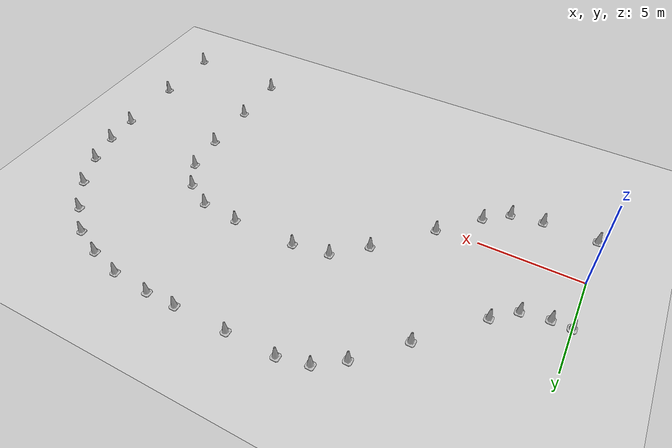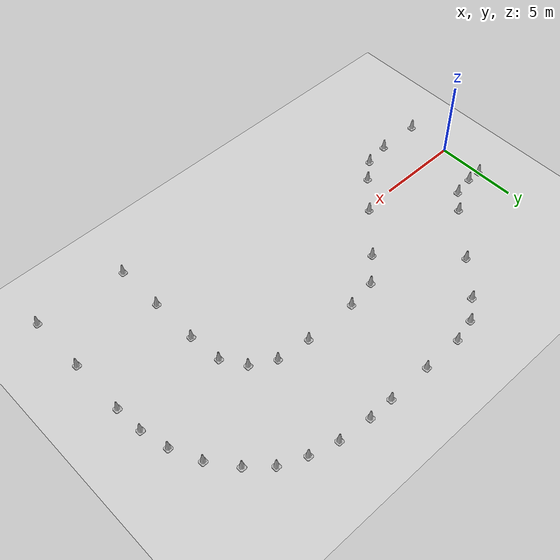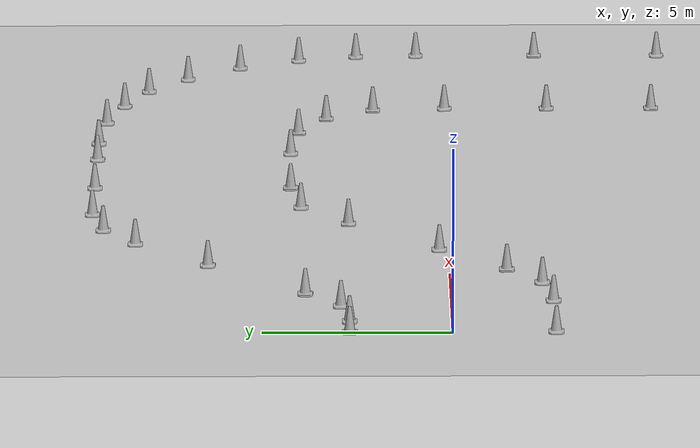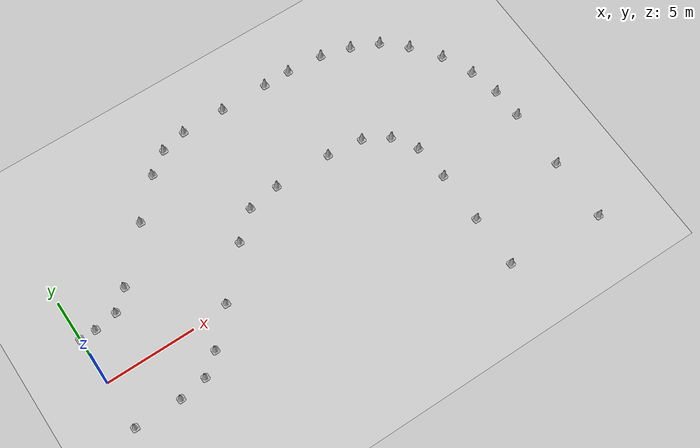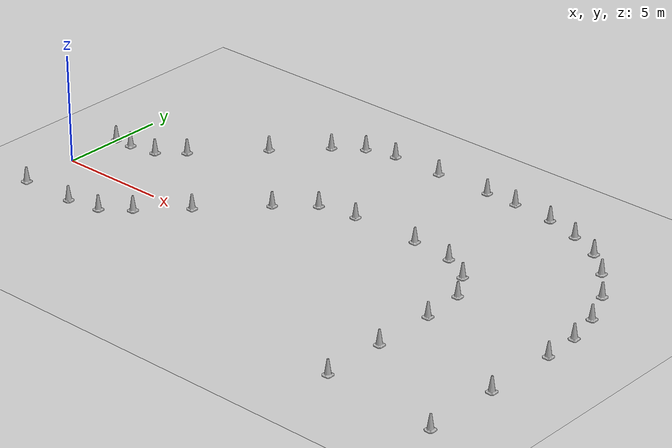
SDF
<sdf version="1.7">
 <world name="default">
  <light name="sun" type="directional">
   <pose>0 0 10 0 -0 0</pose>
   <diffuse>0.8 0.8 0.8 1</diffuse>
   <specular>0.2 0.2 0.2 1</specular>
   <attenuation>
    <range>1000</range>
    <constant>0.9</constant>
    <linear>0.01</linear>
    <quadratic>0.001</quadratic>
   </attenuation>
   <direction>-0.5 0.1 -0.9</direction>
   <spot><inner_angle>0</inner_angle><outer_angle>0</outer_angle><falloff>0</falloff></spot>
  </light>
  <gravity>0 0 -9.8</gravity>
  <magnetic_field>6e-06 2.3e-05 -4.2e-05</magnetic_field>
  <atmosphere type="adiabatic"/>
  <physics type="ode">
   <max_step_size>0.001</max_step_size>
   <real_time_factor>1</real_time_factor>
   <real_time_update_rate>1000</real_time_update_rate>
  </physics>
  <scene><ambient>0.4 0.4 0.4 1</ambient><background>0.7 0.7 0.7 1</background><shadows>1</shadows></scene>
  <spherical_coordinates>
   <surface_model>EARTH_WGS84</surface_model>
   <latitude_deg>0</latitude_deg>
   <longitude_deg>0</longitude_deg>
   <elevation>0</elevation>
   <heading_deg>0</heading_deg>
  </spherical_coordinates>
  <model name="Construction_Cone_b">
   <link name="link">
    <inertial>
     <inertia><ixx>1</ixx><ixy>0</ixy><ixz>0</ixz><iyy>1</iyy><iyz>0</iyz><izz>1</izz></inertia>
     <mass>1</mass>
    </inertial>
    <visual name="visual">
     <geometry>
      <mesh><scale>8 8 6.7</scale><uri>./construction_cone/meshes/construction_cone_b.dae</uri></mesh>
     </geometry>
     <material><shader type="pixel"/></material>
    </visual>
    <collision name="collision">
     <geometry>
      <mesh><uri>./construction_cone/meshes/construction_cone_b.dae</uri><scale>8 8 6.7</scale></mesh>
     </geometry>
     <surface>
      <friction>
       <ode><mu>1</mu><mu2>1</mu2><fdir1>0 0 0</fdir1><slip1>0</slip1><slip2>0</slip2></ode>
       <torsional>
        <coefficient>1</coefficient>
        <patch_radius>0</patch_radius>
        <surface_radius>0</surface_radius>
        <use_patch_radius>1</use_patch_radius>
        <ode><slip>0</slip></ode>
       </torsional>
      </friction>
      <bounce><restitution_coefficient>0</restitution_coefficient><threshold>1e+06</threshold></bounce>
      <contact>
       <collide_without_contact>0</collide_without_contact>
       <collide_without_contact_bitmask>1</collide_without_contact_bitmask>
       <collide_bitmask>1</collide_bitmask>
       <ode>
        <soft_cfm>0</soft_cfm>
        <soft_erp>0.2</soft_erp>
        <kp>1e+13</kp>
        <kd>1</kd>
        <max_vel>0.01</max_vel>
        <min_depth>0</min_depth>
       </ode>
       <bullet>
        <split_impulse>1</split_impulse>
        <split_impulse_penetration_threshold>-0.01</split_impulse_penetration_threshold>
        <soft_cfm>0</soft_cfm>
        <soft_erp>0.2</soft_erp>
        <kp>1e+13</kp>
        <kd>1</kd>
       </bullet>
      </contact>
     </surface>
    </collision>
   </link>
   <static>0</static>
   <pose>0.018257 -2.69927 -0 0 -0 0</pose>
  </model>
  <model name="Construction_Cone_b_1">
   <link name="link">
    <inertial>
     <inertia><ixx>1</ixx><ixy>0</ixy><ixz>0</ixz><iyy>1</iyy><iyz>0</iyz><izz>1</izz></inertia>
     <mass>1</mass>
    </inertial>
    <visual name="visual">
     <geometry>
      <mesh><scale>8 8 6.7</scale><uri>./construction_cone/meshes/construction_cone_b.dae</uri></mesh>
     </geometry>
     <material><shader type="pixel"/></material>
    </visual>
    <collision name="collision">
     <geometry>
      <mesh><uri>./construction_cone/meshes/construction_cone_b.dae</uri><scale>8 8 6.7</scale></mesh>
     </geometry>
     <surface>
      <friction>
       <ode><mu>1</mu><mu2>1</mu2><fdir1>0 0 0</fdir1><slip1>0</slip1><slip2>0</slip2></ode>
       <torsional>
        <coefficient>1</coefficient>
        <patch_radius>0</patch_radius>
        <surface_radius>0</surface_radius>
        <use_patch_radius>1</use_patch_radius>
        <ode><slip>0</slip></ode>
       </torsional>
      </friction>
      <bounce><restitution_coefficient>0</restitution_coefficient><threshold>1e+06</threshold></bounce>
      <contact>
       <collide_without_contact>0</collide_without_contact>
       <collide_without_contact_bitmask>1</collide_without_contact_bitmask>
       <collide_bitmask>1</collide_bitmask>
       <ode>
        <soft_cfm>0</soft_cfm>
        <soft_erp>0.2</soft_erp>
        <kp>1e+13</kp>
        <kd>1</kd>
        <max_vel>0.01</max_vel>
        <min_depth>0</min_depth>
       </ode>
       <bullet>
        <split_impulse>1</split_impulse>
        <split_impulse_penetration_threshold>-0.01</split_impulse_penetration_threshold>
        <soft_cfm>0</soft_cfm>
        <soft_erp>0.2</soft_erp>
        <kp>1e+13</kp>
        <kd>1</kd>
       </bullet>
      </contact>
     </surface>
    </collision>
   </link>
   <static>0</static>
   <pose>2.61619 -2.70033 -0 0 -0 0</pose>
  </model>
  <model name="Construction_Cone_y">
   <link name="link">
    <inertial>
     <inertia><ixx>1</ixx><ixy>0</ixy><ixz>0</ixz><iyy>1</iyy><iyz>0</iyz><izz>1</izz></inertia>
     <mass>1</mass>
    </inertial>
    <visual name="visual">
     <geometry>
      <mesh><scale>8 8 6.7</scale><uri>./construction_cone/meshes/construction_cone_y.dae</uri></mesh>
     </geometry>
     <material><shader type="pixel"/></material>
    </visual>
    <collision name="collision">
     <geometry>
      <mesh><uri>./construction_cone/meshes/construction_cone_y.dae</uri><scale>8 8 6.7</scale></mesh>
     </geometry>
     <surface>
      <friction>
       <ode><mu>1</mu><mu2>1</mu2><fdir1>0 0 0</fdir1><slip1>0</slip1><slip2>0</slip2></ode>
       <torsional>
        <coefficient>1</coefficient>
        <patch_radius>0</patch_radius>
        <surface_radius>0</surface_radius>
        <use_patch_radius>1</use_patch_radius>
        <ode><slip>0</slip></ode>
       </torsional>
      </friction>
      <bounce><restitution_coefficient>0</restitution_coefficient><threshold>1e+06</threshold></bounce>
      <contact>
       <collide_without_contact>0</collide_without_contact>
       <collide_without_contact_bitmask>1</collide_without_contact_bitmask>
       <collide_bitmask>1</collide_bitmask>
       <ode>
        <soft_cfm>0</soft_cfm>
        <soft_erp>0.2</soft_erp>
        <kp>1e+13</kp>
        <kd>1</kd>
        <max_vel>0.01</max_vel>
        <min_depth>0</min_depth>
       </ode>
       <bullet>
        <split_impulse>1</split_impulse>
        <split_impulse_penetration_threshold>-0.01</split_impulse_penetration_threshold>
        <soft_cfm>0</soft_cfm>
        <soft_erp>0.2</soft_erp>
        <kp>1e+13</kp>
        <kd>1</kd>
       </bullet>
      </contact>
     </surface>
    </collision>
   </link>
   <static>0</static>
   <pose>-0.000371 2.70034 -0 0 -0 0</pose>
  </model>
  <model name="Construction_Cone_b_4">
   <link name="link">
    <inertial>
     <inertia><ixx>1</ixx><ixy>0</ixy><ixz>0</ixz><iyy>1</iyy><iyz>0</iyz><izz>1</izz></inertia>
     <mass>1</mass>
    </inertial>
    <visual name="visual">
     <geometry>
      <mesh><scale>8 8 6.7</scale><uri>./construction_cone/meshes/construction_cone_b.dae</uri></mesh>
     </geometry>
     <material><shader type="pixel"/></material>
    </visual>
    <collision name="collision">
     <geometry>
      <mesh><uri>./construction_cone/meshes/construction_cone_b.dae</uri><scale>8 8 6.7</scale></mesh>
     </geometry>
     <surface>
      <friction>
       <ode><mu>1</mu><mu2>1</mu2><fdir1>0 0 0</fdir1><slip1>0</slip1><slip2>0</slip2></ode>
       <torsional>
        <coefficient>1</coefficient>
        <patch_radius>0</patch_radius>
        <surface_radius>0</surface_radius>
        <use_patch_radius>1</use_patch_radius>
        <ode><slip>0</slip></ode>
       </torsional>
      </friction>
      <bounce><restitution_coefficient>0</restitution_coefficient><threshold>1e+06</threshold></bounce>
      <contact>
       <collide_without_contact>0</collide_without_contact>
       <collide_without_contact_bitmask>1</collide_without_contact_bitmask>
       <collide_bitmask>1</collide_bitmask>
       <ode>
        <soft_cfm>0</soft_cfm>
        <soft_erp>0.2</soft_erp>
        <kp>1e+13</kp>
        <kd>1</kd>
        <max_vel>0.01</max_vel>
        <min_depth>0</min_depth>
       </ode>
       <bullet>
        <split_impulse>1</split_impulse>
        <split_impulse_penetration_threshold>-0.01</split_impulse_penetration_threshold>
        <soft_cfm>0</soft_cfm>
        <soft_erp>0.2</soft_erp>
        <kp>1e+13</kp>
        <kd>1</kd>
       </bullet>
      </contact>
     </surface>
    </collision>
   </link>
   <static>0</static>
   <pose>4.16814 -2.4464 -0 0 -0 0</pose>
  </model>
  <model name="Construction_Cone_b_5">
   <link name="link">
    <inertial>
     <inertia><ixx>1</ixx><ixy>0</ixy><ixz>0</ixz><iyy>1</iyy><iyz>0</iyz><izz>1</izz></inertia>
     <mass>1</mass>
    </inertial>
    <visual name="visual">
     <geometry>
      <mesh><scale>8 8 6.7</scale><uri>./construction_cone/meshes/construction_cone_b.dae</uri></mesh>
     </geometry>
     <material><shader type="pixel"/></material>
    </visual>
    <collision name="collision">
     <geometry>
      <mesh><uri>./construction_cone/meshes/construction_cone_b.dae</uri><scale>8 8 6.7</scale></mesh>
     </geometry>
     <surface>
      <friction>
       <ode><mu>1</mu><mu2>1</mu2><fdir1>0 0 0</fdir1><slip1>0</slip1><slip2>0</slip2></ode>
       <torsional>
        <coefficient>1</coefficient>
        <patch_radius>0</patch_radius>
        <surface_radius>0</surface_radius>
        <use_patch_radius>1</use_patch_radius>
        <ode><slip>0</slip></ode>
       </torsional>
      </friction>
      <bounce><restitution_coefficient>0</restitution_coefficient><threshold>1e+06</threshold></bounce>
      <contact>
       <collide_without_contact>0</collide_without_contact>
       <collide_without_contact_bitmask>1</collide_without_contact_bitmask>
       <collide_bitmask>1</collide_bitmask>
       <ode>
        <soft_cfm>0</soft_cfm>
        <soft_erp>0.2</soft_erp>
        <kp>1e+13</kp>
        <kd>1</kd>
        <max_vel>0.01</max_vel>
        <min_depth>0</min_depth>
       </ode>
       <bullet>
        <split_impulse>1</split_impulse>
        <split_impulse_penetration_threshold>-0.01</split_impulse_penetration_threshold>
        <soft_cfm>0</soft_cfm>
        <soft_erp>0.2</soft_erp>
        <kp>1e+13</kp>
        <kd>1</kd>
       </bullet>
      </contact>
     </surface>
    </collision>
   </link>
   <static>0</static>
   <pose>5.31102 -1.52578 -0 -0 -0 -0</pose>
  </model>
  <model name="Construction_Cone_b_6">
   <link name="link">
    <inertial>
     <inertia><ixx>1</ixx><ixy>0</ixy><ixz>0</ixz><iyy>1</iyy><iyz>0</iyz><izz>1</izz></inertia>
     <mass>1</mass>
    </inertial>
    <visual name="visual">
     <geometry>
      <mesh><scale>8 8 6.7</scale><uri>./construction_cone/meshes/construction_cone_b.dae</uri></mesh>
     </geometry>
     <material><shader type="pixel"/></material>
    </visual>
    <collision name="collision">
     <geometry>
      <mesh><uri>./construction_cone/meshes/construction_cone_b.dae</uri><scale>8 8 6.7</scale></mesh>
     </geometry>
     <surface>
      <friction>
       <ode><mu>1</mu><mu2>1</mu2><fdir1>0 0 0</fdir1><slip1>0</slip1><slip2>0</slip2></ode>
       <torsional>
        <coefficient>1</coefficient>
        <patch_radius>0</patch_radius>
        <surface_radius>0</surface_radius>
        <use_patch_radius>1</use_patch_radius>
        <ode><slip>0</slip></ode>
       </torsional>
      </friction>
      <bounce><restitution_coefficient>0</restitution_coefficient><threshold>1e+06</threshold></bounce>
      <contact>
       <collide_without_contact>0</collide_without_contact>
       <collide_without_contact_bitmask>1</collide_without_contact_bitmask>
       <collide_bitmask>1</collide_bitmask>
       <ode>
        <soft_cfm>0</soft_cfm>
        <soft_erp>0.2</soft_erp>
        <kp>1e+13</kp>
        <kd>1</kd>
        <max_vel>0.01</max_vel>
        <min_depth>0</min_depth>
       </ode>
       <bullet>
        <split_impulse>1</split_impulse>
        <split_impulse_penetration_threshold>-0.01</split_impulse_penetration_threshold>
        <soft_cfm>0</soft_cfm>
        <soft_erp>0.2</soft_erp>
        <kp>1e+13</kp>
        <kd>1</kd>
       </bullet>
      </contact>
     </surface>
    </collision>
   </link>
   <static>0</static>
   <pose>9.3905 2.69936 -0 0 -0 0</pose>
  </model>
  <model name="Construction_Cone_b_8">
   <link name="link">
    <inertial>
     <inertia><ixx>1</ixx><ixy>0</ixy><ixz>0</ixz><iyy>1</iyy><iyz>0</iyz><izz>1</izz></inertia>
     <mass>1</mass>
    </inertial>
    <visual name="visual">
     <geometry>
      <mesh><scale>8 8 6.7</scale><uri>./construction_cone/meshes/construction_cone_b.dae</uri></mesh>
     </geometry>
     <material><shader type="pixel"/></material>
    </visual>
    <collision name="collision">
     <geometry>
      <mesh><uri>./construction_cone/meshes/construction_cone_b.dae</uri><scale>8 8 6.7</scale></mesh>
     </geometry>
     <surface>
      <friction>
       <ode><mu>1</mu><mu2>1</mu2><fdir1>0 0 0</fdir1><slip1>0</slip1><slip2>0</slip2></ode>
       <torsional>
        <coefficient>1</coefficient>
        <patch_radius>0</patch_radius>
        <surface_radius>0</surface_radius>
        <use_patch_radius>1</use_patch_radius>
        <ode><slip>0</slip></ode>
       </torsional>
      </friction>
      <bounce><restitution_coefficient>0</restitution_coefficient><threshold>1e+06</threshold></bounce>
      <contact>
       <collide_without_contact>0</collide_without_contact>
       <collide_without_contact_bitmask>1</collide_without_contact_bitmask>
       <collide_bitmask>1</collide_bitmask>
       <ode>
        <soft_cfm>0</soft_cfm>
        <soft_erp>0.2</soft_erp>
        <kp>1e+13</kp>
        <kd>1</kd>
        <max_vel>0.01</max_vel>
        <min_depth>0</min_depth>
       </ode>
       <bullet>
        <split_impulse>1</split_impulse>
        <split_impulse_penetration_threshold>-0.01</split_impulse_penetration_threshold>
        <soft_cfm>0</soft_cfm>
        <soft_erp>0.2</soft_erp>
        <kp>1e+13</kp>
        <kd>1</kd>
       </bullet>
      </contact>
     </surface>
    </collision>
   </link>
   <static>0</static>
   <pose>7.05039 0.255697 -0 0 -0 0</pose>
  </model>
  <model name="Construction_Cone_y_0">
   <link name="link">
    <inertial>
     <inertia><ixx>1</ixx><ixy>0</ixy><ixz>0</ixz><iyy>1</iyy><iyz>0</iyz><izz>1</izz></inertia>
     <mass>1</mass>
    </inertial>
    <visual name="visual">
     <geometry>
      <mesh><scale>8 8 6.7</scale><uri>./construction_cone/meshes/construction_cone_y.dae</uri></mesh>
     </geometry>
     <material><shader type="pixel"/></material>
    </visual>
    <collision name="collision">
     <geometry>
      <mesh><uri>./construction_cone/meshes/construction_cone_y.dae</uri><scale>8 8 6.7</scale></mesh>
     </geometry>
     <surface>
      <friction>
       <ode><mu>1</mu><mu2>1</mu2><fdir1>0 0 0</fdir1><slip1>0</slip1><slip2>0</slip2></ode>
       <torsional>
        <coefficient>1</coefficient>
        <patch_radius>0</patch_radius>
        <surface_radius>0</surface_radius>
        <use_patch_radius>1</use_patch_radius>
        <ode><slip>0</slip></ode>
       </torsional>
      </friction>
      <bounce><restitution_coefficient>0</restitution_coefficient><threshold>1e+06</threshold></bounce>
      <contact>
       <collide_without_contact>0</collide_without_contact>
       <collide_without_contact_bitmask>1</collide_without_contact_bitmask>
       <collide_bitmask>1</collide_bitmask>
       <ode>
        <soft_cfm>0</soft_cfm>
        <soft_erp>0.2</soft_erp>
        <kp>1e+13</kp>
        <kd>1</kd>
        <max_vel>0.01</max_vel>
        <min_depth>0</min_depth>
       </ode>
       <bullet>
        <split_impulse>1</split_impulse>
        <split_impulse_penetration_threshold>-0.01</split_impulse_penetration_threshold>
        <soft_cfm>0</soft_cfm>
        <soft_erp>0.2</soft_erp>
        <kp>1e+13</kp>
        <kd>1</kd>
       </bullet>
      </contact>
     </surface>
    </collision>
   </link>
   <static>0</static>
   <pose>0.895013 2.70094 -0 0 -0 0</pose>
  </model>
  <model name="Construction_Cone_y_2">
   <link name="link">
    <inertial>
     <inertia><ixx>1</ixx><ixy>0</ixy><ixz>0</ixz><iyy>1</iyy><iyz>0</iyz><izz>1</izz></inertia>
     <mass>1</mass>
    </inertial>
    <visual name="visual">
     <geometry>
      <mesh><scale>8 8 6.7</scale><uri>./construction_cone/meshes/construction_cone_y.dae</uri></mesh>
     </geometry>
     <material><shader type="pixel"/></material>
    </visual>
    <collision name="collision">
     <geometry>
      <mesh><uri>./construction_cone/meshes/construction_cone_y.dae</uri><scale>8 8 6.7</scale></mesh>
     </geometry>
     <surface>
      <friction>
       <ode><mu>1</mu><mu2>1</mu2><fdir1>0 0 0</fdir1><slip1>0</slip1><slip2>0</slip2></ode>
       <torsional>
        <coefficient>1</coefficient>
        <patch_radius>0</patch_radius>
        <surface_radius>0</surface_radius>
        <use_patch_radius>1</use_patch_radius>
        <ode><slip>0</slip></ode>
       </torsional>
      </friction>
      <bounce><restitution_coefficient>0</restitution_coefficient><threshold>1e+06</threshold></bounce>
      <contact>
       <collide_without_contact>0</collide_without_contact>
       <collide_without_contact_bitmask>1</collide_without_contact_bitmask>
       <collide_bitmask>1</collide_bitmask>
       <ode>
        <soft_cfm>0</soft_cfm>
        <soft_erp>0.2</soft_erp>
        <kp>1e+13</kp>
        <kd>1</kd>
        <max_vel>0.01</max_vel>
        <min_depth>0</min_depth>
       </ode>
       <bullet>
        <split_impulse>1</split_impulse>
        <split_impulse_penetration_threshold>-0.01</split_impulse_penetration_threshold>
        <soft_cfm>0</soft_cfm>
        <soft_erp>0.2</soft_erp>
        <kp>1e+13</kp>
        <kd>1</kd>
       </bullet>
      </contact>
     </surface>
    </collision>
   </link>
   <static>0</static>
   <pose>2.18883 2.92505 -0 -0 -0 -0</pose>
  </model>
  <model name="Construction_Cone_y_5">
   <link name="link">
    <inertial>
     <inertia><ixx>1</ixx><ixy>0</ixy><ixz>0</ixz><iyy>1</iyy><iyz>0</iyz><izz>1</izz></inertia>
     <mass>1</mass>
    </inertial>
    <visual name="visual">
     <geometry>
      <mesh><scale>8 8 6.7</scale><uri>./construction_cone/meshes/construction_cone_y.dae</uri></mesh>
     </geometry>
     <material><shader type="pixel"/></material>
    </visual>
    <collision name="collision">
     <geometry>
      <mesh><uri>./construction_cone/meshes/construction_cone_y.dae</uri><scale>8 8 6.7</scale></mesh>
     </geometry>
     <surface>
      <friction>
       <ode><mu>1</mu><mu2>1</mu2><fdir1>0 0 0</fdir1><slip1>0</slip1><slip2>0</slip2></ode>
       <torsional>
        <coefficient>1</coefficient>
        <patch_radius>0</patch_radius>
        <surface_radius>0</surface_radius>
        <use_patch_radius>1</use_patch_radius>
        <ode><slip>0</slip></ode>
       </torsional>
      </friction>
      <bounce><restitution_coefficient>0</restitution_coefficient><threshold>1e+06</threshold></bounce>
      <contact>
       <collide_without_contact>0</collide_without_contact>
       <collide_without_contact_bitmask>1</collide_without_contact_bitmask>
       <collide_bitmask>1</collide_bitmask>
       <ode>
        <soft_cfm>0</soft_cfm>
        <soft_erp>0.2</soft_erp>
        <kp>1e+13</kp>
        <kd>1</kd>
        <max_vel>0.01</max_vel>
        <min_depth>0</min_depth>
       </ode>
       <bullet>
        <split_impulse>1</split_impulse>
        <split_impulse_penetration_threshold>-0.01</split_impulse_penetration_threshold>
        <soft_cfm>0</soft_cfm>
        <soft_erp>0.2</soft_erp>
        <kp>1e+13</kp>
        <kd>1</kd>
       </bullet>
      </contact>
     </surface>
    </collision>
   </link>
   <static>0</static>
   <pose>3.23745 3.86585 -0 0 -0 0</pose>
  </model>
  <model name="Construction_Cone_b_10">
   <link name="link">
    <inertial>
     <inertia><ixx>1</ixx><ixy>0</ixy><ixz>0</ixz><iyy>1</iyy><iyz>0</iyz><izz>1</izz></inertia>
     <mass>1</mass>
    </inertial>
    <visual name="visual">
     <geometry>
      <mesh><scale>8 8 6.7</scale><uri>./construction_cone/meshes/construction_cone_b.dae</uri></mesh>
     </geometry>
     <material><shader type="pixel"/></material>
    </visual>
    <collision name="collision">
     <geometry>
      <mesh><uri>./construction_cone/meshes/construction_cone_b.dae</uri><scale>8 8 6.7</scale></mesh>
     </geometry>
     <surface>
      <friction>
       <ode><mu>1</mu><mu2>1</mu2><fdir1>0 0 0</fdir1><slip1>0</slip1><slip2>0</slip2></ode>
       <torsional>
        <coefficient>1</coefficient>
        <patch_radius>0</patch_radius>
        <surface_radius>0</surface_radius>
        <use_patch_radius>1</use_patch_radius>
        <ode><slip>0</slip></ode>
       </torsional>
      </friction>
      <bounce><restitution_coefficient>0</restitution_coefficient><threshold>1e+06</threshold></bounce>
      <contact>
       <collide_without_contact>0</collide_without_contact>
       <collide_without_contact_bitmask>1</collide_without_contact_bitmask>
       <collide_bitmask>1</collide_bitmask>
       <ode>
        <soft_cfm>0</soft_cfm>
        <soft_erp>0.2</soft_erp>
        <kp>1e+13</kp>
        <kd>1</kd>
        <max_vel>0.01</max_vel>
        <min_depth>0</min_depth>
       </ode>
       <bullet>
        <split_impulse>1</split_impulse>
        <split_impulse_penetration_threshold>-0.01</split_impulse_penetration_threshold>
        <soft_cfm>0</soft_cfm>
        <soft_erp>0.2</soft_erp>
        <kp>1e+13</kp>
        <kd>1</kd>
       </bullet>
      </contact>
     </surface>
    </collision>
   </link>
   <static>0</static>
   <pose>10.8741 3.99909 -0 0 -0 0</pose>
  </model>
  <model name="Construction_Cone_b_13">
   <link name="link">
    <inertial>
     <inertia><ixx>1</ixx><ixy>0</ixy><ixz>0</ixz><iyy>1</iyy><iyz>0</iyz><izz>1</izz></inertia>
     <mass>1</mass>
    </inertial>
    <visual name="visual">
     <geometry>
      <mesh><scale>8 8 6.7</scale><uri>./construction_cone/meshes/construction_cone_b.dae</uri></mesh>
     </geometry>
     <material><shader type="pixel"/></material>
    </visual>
    <collision name="collision">
     <geometry>
      <mesh><uri>./construction_cone/meshes/construction_cone_b.dae</uri><scale>8 8 6.7</scale></mesh>
     </geometry>
     <surface>
      <friction>
       <ode><mu>1</mu><mu2>1</mu2><fdir1>0 0 0</fdir1><slip1>0</slip1><slip2>0</slip2></ode>
       <torsional>
        <coefficient>1</coefficient>
        <patch_radius>0</patch_radius>
        <surface_radius>0</surface_radius>
        <use_patch_radius>1</use_patch_radius>
        <ode><slip>0</slip></ode>
       </torsional>
      </friction>
      <bounce><restitution_coefficient>0</restitution_coefficient><threshold>1e+06</threshold></bounce>
      <contact>
       <collide_without_contact>0</collide_without_contact>
       <collide_without_contact_bitmask>1</collide_without_contact_bitmask>
       <collide_bitmask>1</collide_bitmask>
       <ode>
        <soft_cfm>0</soft_cfm>
        <soft_erp>0.2</soft_erp>
        <kp>1e+13</kp>
        <kd>1</kd>
        <max_vel>0.01</max_vel>
        <min_depth>0</min_depth>
       </ode>
       <bullet>
        <split_impulse>1</split_impulse>
        <split_impulse_penetration_threshold>-0.01</split_impulse_penetration_threshold>
        <soft_cfm>0</soft_cfm>
        <soft_erp>0.2</soft_erp>
        <kp>1e+13</kp>
        <kd>1</kd>
       </bullet>
      </contact>
     </surface>
    </collision>
   </link>
   <static>0</static>
   <pose>12.6908 4.28602 -0 -0 -0 -0</pose>
  </model>
  <model name="Construction_Cone_b_15">
   <link name="link">
    <inertial>
     <inertia><ixx>1</ixx><ixy>0</ixy><ixz>0</ixz><iyy>1</iyy><iyz>0</iyz><izz>1</izz></inertia>
     <mass>1</mass>
    </inertial>
    <visual name="visual">
     <geometry>
      <mesh><scale>8 8 6.7</scale><uri>./construction_cone/meshes/construction_cone_b.dae</uri></mesh>
     </geometry>
     <material><shader type="pixel"/></material>
    </visual>
    <collision name="collision">
     <geometry>
      <mesh><uri>./construction_cone/meshes/construction_cone_b.dae</uri><scale>8 8 6.7</scale></mesh>
     </geometry>
     <surface>
      <friction>
       <ode><mu>1</mu><mu2>1</mu2><fdir1>0 0 0</fdir1><slip1>0</slip1><slip2>0</slip2></ode>
       <torsional>
        <coefficient>1</coefficient>
        <patch_radius>0</patch_radius>
        <surface_radius>0</surface_radius>
        <use_patch_radius>1</use_patch_radius>
        <ode><slip>0</slip></ode>
       </torsional>
      </friction>
      <bounce><restitution_coefficient>0</restitution_coefficient><threshold>1e+06</threshold></bounce>
      <contact>
       <collide_without_contact>0</collide_without_contact>
       <collide_without_contact_bitmask>1</collide_without_contact_bitmask>
       <collide_bitmask>1</collide_bitmask>
       <ode>
        <soft_cfm>0</soft_cfm>
        <soft_erp>0.2</soft_erp>
        <kp>1e+13</kp>
        <kd>1</kd>
        <max_vel>0.01</max_vel>
        <min_depth>0</min_depth>
       </ode>
       <bullet>
        <split_impulse>1</split_impulse>
        <split_impulse_penetration_threshold>-0.01</split_impulse_penetration_threshold>
        <soft_cfm>0</soft_cfm>
        <soft_erp>0.2</soft_erp>
        <kp>1e+13</kp>
        <kd>1</kd>
       </bullet>
      </contact>
     </surface>
    </collision>
   </link>
   <static>0</static>
   <pose>15.9301 4.29807 -0 0 -0 0</pose>
  </model>
  <model name="Construction_Cone_b_17">
   <link name="link">
    <inertial>
     <inertia><ixx>1</ixx><ixy>0</ixy><ixz>0</ixz><iyy>1</iyy><iyz>0</iyz><izz>1</izz></inertia>
     <mass>1</mass>
    </inertial>
    <visual name="visual">
     <geometry>
      <mesh><scale>8 8 6.7</scale><uri>./construction_cone/meshes/construction_cone_b.dae</uri></mesh>
     </geometry>
     <material><shader type="pixel"/></material>
    </visual>
    <collision name="collision">
     <geometry>
      <mesh><uri>./construction_cone/meshes/construction_cone_b.dae</uri><scale>8 8 6.7</scale></mesh>
     </geometry>
     <surface>
      <friction>
       <ode><mu>1</mu><mu2>1</mu2><fdir1>0 0 0</fdir1><slip1>0</slip1><slip2>0</slip2></ode>
       <torsional>
        <coefficient>1</coefficient>
        <patch_radius>0</patch_radius>
        <surface_radius>0</surface_radius>
        <use_patch_radius>1</use_patch_radius>
        <ode><slip>0</slip></ode>
       </torsional>
      </friction>
      <bounce><restitution_coefficient>0</restitution_coefficient><threshold>1e+06</threshold></bounce>
      <contact>
       <collide_without_contact>0</collide_without_contact>
       <collide_without_contact_bitmask>1</collide_without_contact_bitmask>
       <collide_bitmask>1</collide_bitmask>
       <ode>
        <soft_cfm>0</soft_cfm>
        <soft_erp>0.2</soft_erp>
        <kp>1e+13</kp>
        <kd>1</kd>
        <max_vel>0.01</max_vel>
        <min_depth>0</min_depth>
       </ode>
       <bullet>
        <split_impulse>1</split_impulse>
        <split_impulse_penetration_threshold>-0.01</split_impulse_penetration_threshold>
        <soft_cfm>0</soft_cfm>
        <soft_erp>0.2</soft_erp>
        <kp>1e+13</kp>
        <kd>1</kd>
       </bullet>
      </contact>
     </surface>
    </collision>
   </link>
   <static>0</static>
   <pose>17.934 4.08187 -0 -0 -0 -0</pose>
  </model>
  <model name="Construction_Cone_b_18">
   <link name="link">
    <inertial>
     <inertia><ixx>1</ixx><ixy>0</ixy><ixz>0</ixz><iyy>1</iyy><iyz>0</iyz><izz>1</izz></inertia>
     <mass>1</mass>
    </inertial>
    <visual name="visual">
     <geometry>
      <mesh><scale>8 8 6.7</scale><uri>./construction_cone/meshes/construction_cone_b.dae</uri></mesh>
     </geometry>
     <material><shader type="pixel"/></material>
    </visual>
    <collision name="collision">
     <geometry>
      <mesh><uri>./construction_cone/meshes/construction_cone_b.dae</uri><scale>8 8 6.7</scale></mesh>
     </geometry>
     <surface>
      <friction>
       <ode><mu>1</mu><mu2>1</mu2><fdir1>0 0 0</fdir1><slip1>0</slip1><slip2>0</slip2></ode>
       <torsional>
        <coefficient>1</coefficient>
        <patch_radius>0</patch_radius>
        <surface_radius>0</surface_radius>
        <use_patch_radius>1</use_patch_radius>
        <ode><slip>0</slip></ode>
       </torsional>
      </friction>
      <bounce><restitution_coefficient>0</restitution_coefficient><threshold>1e+06</threshold></bounce>
      <contact>
       <collide_without_contact>0</collide_without_contact>
       <collide_without_contact_bitmask>1</collide_without_contact_bitmask>
       <collide_bitmask>1</collide_bitmask>
       <ode>
        <soft_cfm>0</soft_cfm>
        <soft_erp>0.2</soft_erp>
        <kp>1e+13</kp>
        <kd>1</kd>
        <max_vel>0.01</max_vel>
        <min_depth>0</min_depth>
       </ode>
       <bullet>
        <split_impulse>1</split_impulse>
        <split_impulse_penetration_threshold>-0.01</split_impulse_penetration_threshold>
        <soft_cfm>0</soft_cfm>
        <soft_erp>0.2</soft_erp>
        <kp>1e+13</kp>
        <kd>1</kd>
       </bullet>
      </contact>
     </surface>
    </collision>
   </link>
   <static>0</static>
   <pose>19.3008 3.29623 -0 0 -0 0</pose>
  </model>
  <model name="Construction_Cone_b_19">
   <link name="link">
    <inertial>
     <inertia><ixx>1</ixx><ixy>0</ixy><ixz>0</ixz><iyy>1</iyy><iyz>0</iyz><izz>1</izz></inertia>
     <mass>1</mass>
    </inertial>
    <visual name="visual">
     <geometry>
      <mesh><scale>8 8 6.7</scale><uri>./construction_cone/meshes/construction_cone_b.dae</uri></mesh>
     </geometry>
     <material><shader type="pixel"/></material>
    </visual>
    <collision name="collision">
     <geometry>
      <mesh><uri>./construction_cone/meshes/construction_cone_b.dae</uri><scale>8 8 6.7</scale></mesh>
     </geometry>
     <surface>
      <friction>
       <ode><mu>1</mu><mu2>1</mu2><fdir1>0 0 0</fdir1><slip1>0</slip1><slip2>0</slip2></ode>
       <torsional>
        <coefficient>1</coefficient>
        <patch_radius>0</patch_radius>
        <surface_radius>0</surface_radius>
        <use_patch_radius>1</use_patch_radius>
        <ode><slip>0</slip></ode>
       </torsional>
      </friction>
      <bounce><restitution_coefficient>0</restitution_coefficient><threshold>1e+06</threshold></bounce>
      <contact>
       <collide_without_contact>0</collide_without_contact>
       <collide_without_contact_bitmask>1</collide_without_contact_bitmask>
       <collide_bitmask>1</collide_bitmask>
       <ode>
        <soft_cfm>0</soft_cfm>
        <soft_erp>0.2</soft_erp>
        <kp>1e+13</kp>
        <kd>1</kd>
        <max_vel>0.01</max_vel>
        <min_depth>0</min_depth>
       </ode>
       <bullet>
        <split_impulse>1</split_impulse>
        <split_impulse_penetration_threshold>-0.01</split_impulse_penetration_threshold>
        <soft_cfm>0</soft_cfm>
        <soft_erp>0.2</soft_erp>
        <kp>1e+13</kp>
        <kd>1</kd>
       </bullet>
      </contact>
     </surface>
    </collision>
   </link>
   <static>0</static>
   <pose>20.142 1.96534 -0 -0 -0 -0</pose>
  </model>
  <model name="Construction_Cone_b_20">
   <link name="link">
    <inertial>
     <inertia><ixx>1</ixx><ixy>0</ixy><ixz>0</ixz><iyy>1</iyy><iyz>0</iyz><izz>1</izz></inertia>
     <mass>1</mass>
    </inertial>
    <visual name="visual">
     <geometry>
      <mesh><scale>8 8 6.7</scale><uri>./construction_cone/meshes/construction_cone_b.dae</uri></mesh>
     </geometry>
     <material><shader type="pixel"/></material>
    </visual>
    <collision name="collision">
     <geometry>
      <mesh><uri>./construction_cone/meshes/construction_cone_b.dae</uri><scale>8 8 6.7</scale></mesh>
     </geometry>
     <surface>
      <friction>
       <ode><mu>1</mu><mu2>1</mu2><fdir1>0 0 0</fdir1><slip1>0</slip1><slip2>0</slip2></ode>
       <torsional>
        <coefficient>1</coefficient>
        <patch_radius>0</patch_radius>
        <surface_radius>0</surface_radius>
        <use_patch_radius>1</use_patch_radius>
        <ode><slip>0</slip></ode>
       </torsional>
      </friction>
      <bounce><restitution_coefficient>0</restitution_coefficient><threshold>1e+06</threshold></bounce>
      <contact>
       <collide_without_contact>0</collide_without_contact>
       <collide_without_contact_bitmask>1</collide_without_contact_bitmask>
       <collide_bitmask>1</collide_bitmask>
       <ode>
        <soft_cfm>0</soft_cfm>
        <soft_erp>0.2</soft_erp>
        <kp>1e+13</kp>
        <kd>1</kd>
        <max_vel>0.01</max_vel>
        <min_depth>0</min_depth>
       </ode>
       <bullet>
        <split_impulse>1</split_impulse>
        <split_impulse_penetration_threshold>-0.01</split_impulse_penetration_threshold>
        <soft_cfm>0</soft_cfm>
        <soft_erp>0.2</soft_erp>
        <kp>1e+13</kp>
        <kd>1</kd>
       </bullet>
      </contact>
     </surface>
    </collision>
   </link>
   <static>0</static>
   <pose>20.3057 -0.077252 -0 0 -0 0</pose>
  </model>
  <model name="Construction_Cone_b_22">
   <link name="link">
    <inertial>
     <inertia><ixx>1</ixx><ixy>0</ixy><ixz>0</ixz><iyy>1</iyy><iyz>0</iyz><izz>1</izz></inertia>
     <mass>1</mass>
    </inertial>
    <visual name="visual">
     <geometry>
      <mesh><scale>8 8 6.7</scale><uri>./construction_cone/meshes/construction_cone_b.dae</uri></mesh>
     </geometry>
     <material><shader type="pixel"/></material>
    </visual>
    <collision name="collision">
     <geometry>
      <mesh><uri>./construction_cone/meshes/construction_cone_b.dae</uri><scale>8 8 6.7</scale></mesh>
     </geometry>
     <surface>
      <friction>
       <ode><mu>1</mu><mu2>1</mu2><fdir1>0 0 0</fdir1><slip1>0</slip1><slip2>0</slip2></ode>
       <torsional>
        <coefficient>1</coefficient>
        <patch_radius>0</patch_radius>
        <surface_radius>0</surface_radius>
        <use_patch_radius>1</use_patch_radius>
        <ode><slip>0</slip></ode>
       </torsional>
      </friction>
      <bounce><restitution_coefficient>0</restitution_coefficient><threshold>1e+06</threshold></bounce>
      <contact>
       <collide_without_contact>0</collide_without_contact>
       <collide_without_contact_bitmask>1</collide_without_contact_bitmask>
       <collide_bitmask>1</collide_bitmask>
       <ode>
        <soft_cfm>0</soft_cfm>
        <soft_erp>0.2</soft_erp>
        <kp>1e+13</kp>
        <kd>1</kd>
        <max_vel>0.01</max_vel>
        <min_depth>0</min_depth>
       </ode>
       <bullet>
        <split_impulse>1</split_impulse>
        <split_impulse_penetration_threshold>-0.01</split_impulse_penetration_threshold>
        <soft_cfm>0</soft_cfm>
        <soft_erp>0.2</soft_erp>
        <kp>1e+13</kp>
        <kd>1</kd>
       </bullet>
      </contact>
     </surface>
    </collision>
   </link>
   <static>0</static>
   <pose>20.304 -2.99768 -0 0 -0 0</pose>
  </model>
  <model name="Construction_Cone_b_23">
   <link name="link">
    <inertial>
     <inertia><ixx>1</ixx><ixy>0</ixy><ixz>0</ixz><iyy>1</iyy><iyz>0</iyz><izz>1</izz></inertia>
     <mass>1</mass>
    </inertial>
    <visual name="visual">
     <geometry>
      <mesh><scale>8 8 6.7</scale><uri>./construction_cone/meshes/construction_cone_b.dae</uri></mesh>
     </geometry>
     <material><shader type="pixel"/></material>
    </visual>
    <collision name="collision">
     <geometry>
      <mesh><uri>./construction_cone/meshes/construction_cone_b.dae</uri><scale>8 8 6.7</scale></mesh>
     </geometry>
     <surface>
      <friction>
       <ode><mu>1</mu><mu2>1</mu2><fdir1>0 0 0</fdir1><slip1>0</slip1><slip2>0</slip2></ode>
       <torsional>
        <coefficient>1</coefficient>
        <patch_radius>0</patch_radius>
        <surface_radius>0</surface_radius>
        <use_patch_radius>1</use_patch_radius>
        <ode><slip>0</slip></ode>
       </torsional>
      </friction>
      <bounce><restitution_coefficient>0</restitution_coefficient><threshold>1e+06</threshold></bounce>
      <contact>
       <collide_without_contact>0</collide_without_contact>
       <collide_without_contact_bitmask>1</collide_without_contact_bitmask>
       <collide_bitmask>1</collide_bitmask>
       <ode>
        <soft_cfm>0</soft_cfm>
        <soft_erp>0.2</soft_erp>
        <kp>1e+13</kp>
        <kd>1</kd>
        <max_vel>0.01</max_vel>
        <min_depth>0</min_depth>
       </ode>
       <bullet>
        <split_impulse>1</split_impulse>
        <split_impulse_penetration_threshold>-0.01</split_impulse_penetration_threshold>
        <soft_cfm>0</soft_cfm>
        <soft_erp>0.2</soft_erp>
        <kp>1e+13</kp>
        <kd>1</kd>
       </bullet>
      </contact>
     </surface>
    </collision>
   </link>
   <static>0</static>
   <pose>20.311 -5.9907 -0 -0 -0 -0</pose>
  </model>
  <model name="Construction_Cone_y_10">
   <link name="link">
    <inertial>
     <pose>0 0 0.1 0 -0 0</pose>
     <inertia><ixx>1</ixx><ixy>0</ixy><ixz>0</ixz><iyy>1</iyy><iyz>0</iyz><izz>1</izz></inertia>
     <mass>1</mass>
    </inertial>
    <pose>0 0 0.1 0 -0 0</pose>
    <visual name="visual">
     <geometry>
      <mesh><scale>8 8 6.7</scale><uri>./construction_cone/meshes/construction_cone_y.dae</uri></mesh>
     </geometry>
     <material><shader type="pixel"/></material>
     <pose>0 0 0.1 0 -0 0</pose>
    </visual>
    <collision name="collision">
     <pose>0 0 0.1 0 -0 0</pose>
     <geometry>
      <mesh><uri>./construction_cone/meshes/construction_cone_y.dae</uri><scale>8 8 6.7</scale></mesh>
     </geometry>
     <surface>
      <friction>
       <ode><mu>1</mu><mu2>1</mu2><fdir1>0 0 0</fdir1><slip1>0</slip1><slip2>0</slip2></ode>
       <torsional>
        <coefficient>1</coefficient>
        <patch_radius>0</patch_radius>
        <surface_radius>0</surface_radius>
        <use_patch_radius>1</use_patch_radius>
        <ode><slip>0</slip></ode>
       </torsional>
      </friction>
      <bounce><restitution_coefficient>0</restitution_coefficient><threshold>1e+06</threshold></bounce>
      <contact>
       <collide_without_contact>0</collide_without_contact>
       <collide_without_contact_bitmask>1</collide_without_contact_bitmask>
       <collide_bitmask>1</collide_bitmask>
       <ode>
        <soft_cfm>0</soft_cfm>
        <soft_erp>0.2</soft_erp>
        <kp>1e+13</kp>
        <kd>1</kd>
        <max_vel>0.01</max_vel>
        <min_depth>0</min_depth>
       </ode>
       <bullet>
        <split_impulse>1</split_impulse>
        <split_impulse_penetration_threshold>-0.01</split_impulse_penetration_threshold>
        <soft_cfm>0</soft_cfm>
        <soft_erp>0.2</soft_erp>
        <kp>1e+13</kp>
        <kd>1</kd>
       </bullet>
      </contact>
     </surface>
    </collision>
   </link>
   <static>0</static>
   <pose>5.71191 6.48317 -0.2 0 -0 0</pose>
  </model>
  <model name="Construction_Cone_y_12">
   <link name="link">
    <inertial>
     <pose>0 0 0.1 0 -0 0</pose>
     <inertia><ixx>1</ixx><ixy>0</ixy><ixz>0</ixz><iyy>1</iyy><iyz>0</iyz><izz>1</izz></inertia>
     <mass>1</mass>
    </inertial>
    <pose>0 0 0.1 0 -0 0</pose>
    <visual name="visual">
     <geometry>
      <mesh><scale>8 8 6.7</scale><uri>./construction_cone/meshes/construction_cone_y.dae</uri></mesh>
     </geometry>
     <material><shader type="pixel"/></material>
     <pose>0 0 0.1 0 -0 0</pose>
    </visual>
    <collision name="collision">
     <pose>0 0 0.1 0 -0 0</pose>
     <geometry>
      <mesh><uri>./construction_cone/meshes/construction_cone_y.dae</uri><scale>8 8 6.7</scale></mesh>
     </geometry>
     <surface>
      <friction>
       <ode><mu>1</mu><mu2>1</mu2><fdir1>0 0 0</fdir1><slip1>0</slip1><slip2>0</slip2></ode>
       <torsional>
        <coefficient>1</coefficient>
        <patch_radius>0</patch_radius>
        <surface_radius>0</surface_radius>
        <use_patch_radius>1</use_patch_radius>
        <ode><slip>0</slip></ode>
       </torsional>
      </friction>
      <bounce><restitution_coefficient>0</restitution_coefficient><threshold>1e+06</threshold></bounce>
      <contact>
       <collide_without_contact>0</collide_without_contact>
       <collide_without_contact_bitmask>1</collide_without_contact_bitmask>
       <collide_bitmask>1</collide_bitmask>
       <ode>
        <soft_cfm>0</soft_cfm>
        <soft_erp>0.2</soft_erp>
        <kp>1e+13</kp>
        <kd>1</kd>
        <max_vel>0.01</max_vel>
        <min_depth>0</min_depth>
       </ode>
       <bullet>
        <split_impulse>1</split_impulse>
        <split_impulse_penetration_threshold>-0.01</split_impulse_penetration_threshold>
        <soft_cfm>0</soft_cfm>
        <soft_erp>0.2</soft_erp>
        <kp>1e+13</kp>
        <kd>1</kd>
       </bullet>
      </contact>
     </surface>
    </collision>
   </link>
   <static>0</static>
   <pose>8.83378 9.37105 -0.2 0 -0 0</pose>
  </model>
  <model name="Construction_Cone_y_14">
   <link name="link">
    <inertial>
     <pose>0 0 0.1 0 -0 0</pose>
     <inertia><ixx>1</ixx><ixy>0</ixy><ixz>0</ixz><iyy>1</iyy><iyz>0</iyz><izz>1</izz></inertia>
     <mass>1</mass>
    </inertial>
    <pose>0 0 0.1 0 -0 0</pose>
    <visual name="visual">
     <geometry>
      <mesh><scale>8 8 6.7</scale><uri>./construction_cone/meshes/construction_cone_y.dae</uri></mesh>
     </geometry>
     <material><shader type="pixel"/></material>
     <pose>0 0 0.1 0 -0 0</pose>
    </visual>
    <collision name="collision">
     <pose>0 0 0.1 0 -0 0</pose>
     <geometry>
      <mesh><uri>./construction_cone/meshes/construction_cone_y.dae</uri><scale>8 8 6.7</scale></mesh>
     </geometry>
     <surface>
      <friction>
       <ode><mu>1</mu><mu2>1</mu2><fdir1>0 0 0</fdir1><slip1>0</slip1><slip2>0</slip2></ode>
       <torsional>
        <coefficient>1</coefficient>
        <patch_radius>0</patch_radius>
        <surface_radius>0</surface_radius>
        <use_patch_radius>1</use_patch_radius>
        <ode><slip>0</slip></ode>
       </torsional>
      </friction>
      <bounce><restitution_coefficient>0</restitution_coefficient><threshold>1e+06</threshold></bounce>
      <contact>
       <collide_without_contact>0</collide_without_contact>
       <collide_without_contact_bitmask>1</collide_without_contact_bitmask>
       <collide_bitmask>1</collide_bitmask>
       <ode>
        <soft_cfm>0</soft_cfm>
        <soft_erp>0.2</soft_erp>
        <kp>1e+13</kp>
        <kd>1</kd>
        <max_vel>0.01</max_vel>
        <min_depth>0</min_depth>
       </ode>
       <bullet>
        <split_impulse>1</split_impulse>
        <split_impulse_penetration_threshold>-0.01</split_impulse_penetration_threshold>
        <soft_cfm>0</soft_cfm>
        <soft_erp>0.2</soft_erp>
        <kp>1e+13</kp>
        <kd>1</kd>
       </bullet>
      </contact>
     </surface>
    </collision>
   </link>
   <static>0</static>
   <pose>10.2679 9.70252 -0.2 -0 -0 -0</pose>
  </model>
  <model name="Construction_Cone_y_16">
   <link name="link">
    <inertial>
     <pose>0 0 0.1 0 -0 0</pose>
     <inertia><ixx>1</ixx><ixy>0</ixy><ixz>0</ixz><iyy>1</iyy><iyz>0</iyz><izz>1</izz></inertia>
     <mass>1</mass>
    </inertial>
    <pose>0 0 0.1 0 -0 0</pose>
    <visual name="visual">
     <geometry>
      <mesh><scale>8 8 6.7</scale><uri>./construction_cone/meshes/construction_cone_y.dae</uri></mesh>
     </geometry>
     <material><shader type="pixel"/></material>
     <pose>0 0 0.1 0 -0 0</pose>
    </visual>
    <collision name="collision">
     <pose>0 0 0.1 0 -0 0</pose>
     <geometry>
      <mesh><uri>./construction_cone/meshes/construction_cone_y.dae</uri><scale>8 8 6.7</scale></mesh>
     </geometry>
     <surface>
      <friction>
       <ode><mu>1</mu><mu2>1</mu2><fdir1>0 0 0</fdir1><slip1>0</slip1><slip2>0</slip2></ode>
       <torsional>
        <coefficient>1</coefficient>
        <patch_radius>0</patch_radius>
        <surface_radius>0</surface_radius>
        <use_patch_radius>1</use_patch_radius>
        <ode><slip>0</slip></ode>
       </torsional>
      </friction>
      <bounce><restitution_coefficient>0</restitution_coefficient><threshold>1e+06</threshold></bounce>
      <contact>
       <collide_without_contact>0</collide_without_contact>
       <collide_without_contact_bitmask>1</collide_without_contact_bitmask>
       <collide_bitmask>1</collide_bitmask>
       <ode>
        <soft_cfm>0</soft_cfm>
        <soft_erp>0.2</soft_erp>
        <kp>1e+13</kp>
        <kd>1</kd>
        <max_vel>0.01</max_vel>
        <min_depth>0</min_depth>
       </ode>
       <bullet>
        <split_impulse>1</split_impulse>
        <split_impulse_penetration_threshold>-0.01</split_impulse_penetration_threshold>
        <soft_cfm>0</soft_cfm>
        <soft_erp>0.2</soft_erp>
        <kp>1e+13</kp>
        <kd>1</kd>
       </bullet>
      </contact>
     </surface>
    </collision>
   </link>
   <static>0</static>
   <pose>12.7158 9.70322 -0.2 0 -0 0</pose>
  </model>
  <model name="Construction_Cone_y_18">
   <link name="link">
    <inertial>
     <pose>0 0 0.1 0 -0 0</pose>
     <inertia><ixx>1</ixx><ixy>0</ixy><ixz>0</ixz><iyy>1</iyy><iyz>0</iyz><izz>1</izz></inertia>
     <mass>1</mass>
    </inertial>
    <pose>0 0 0.1 0 -0 0</pose>
    <visual name="visual">
     <geometry>
      <mesh><scale>8 8 6.7</scale><uri>./construction_cone/meshes/construction_cone_y.dae</uri></mesh>
     </geometry>
     <material><shader type="pixel"/></material>
     <pose>0 0 0.1 0 -0 0</pose>
    </visual>
    <collision name="collision">
     <pose>0 0 0.1 0 -0 0</pose>
     <geometry>
      <mesh><uri>./construction_cone/meshes/construction_cone_y.dae</uri><scale>8 8 6.7</scale></mesh>
     </geometry>
     <surface>
      <friction>
       <ode><mu>1</mu><mu2>1</mu2><fdir1>0 0 0</fdir1><slip1>0</slip1><slip2>0</slip2></ode>
       <torsional>
        <coefficient>1</coefficient>
        <patch_radius>0</patch_radius>
        <surface_radius>0</surface_radius>
        <use_patch_radius>1</use_patch_radius>
        <ode><slip>0</slip></ode>
       </torsional>
      </friction>
      <bounce><restitution_coefficient>0</restitution_coefficient><threshold>1e+06</threshold></bounce>
      <contact>
       <collide_without_contact>0</collide_without_contact>
       <collide_without_contact_bitmask>1</collide_without_contact_bitmask>
       <collide_bitmask>1</collide_bitmask>
       <ode>
        <soft_cfm>0</soft_cfm>
        <soft_erp>0.2</soft_erp>
        <kp>1e+13</kp>
        <kd>1</kd>
        <max_vel>0.01</max_vel>
        <min_depth>0</min_depth>
       </ode>
       <bullet>
        <split_impulse>1</split_impulse>
        <split_impulse_penetration_threshold>-0.01</split_impulse_penetration_threshold>
        <soft_cfm>0</soft_cfm>
        <soft_erp>0.2</soft_erp>
        <kp>1e+13</kp>
        <kd>1</kd>
       </bullet>
      </contact>
     </surface>
    </collision>
   </link>
   <static>0</static>
   <pose>15.404 9.70049 -0.2 -0 -0 -0</pose>
  </model>
  <model name="Construction_Cone_y_21">
   <link name="link">
    <inertial>
     <pose>0 0 0.1 0 -0 0</pose>
     <inertia><ixx>1</ixx><ixy>0</ixy><ixz>0</ixz><iyy>1</iyy><iyz>0</iyz><izz>1</izz></inertia>
     <mass>1</mass>
    </inertial>
    <pose>0 0 0.1 0 -0 0</pose>
    <visual name="visual">
     <geometry>
      <mesh><scale>8 8 6.7</scale><uri>./construction_cone/meshes/construction_cone_y.dae</uri></mesh>
     </geometry>
     <material><shader type="pixel"/></material>
     <pose>0 0 0.1 0 -0 0</pose>
    </visual>
    <collision name="collision">
     <pose>0 0 0.1 0 -0 0</pose>
     <geometry>
      <mesh><uri>./construction_cone/meshes/construction_cone_y.dae</uri><scale>8 8 6.7</scale></mesh>
     </geometry>
     <surface>
      <friction>
       <ode><mu>1</mu><mu2>1</mu2><fdir1>0 0 0</fdir1><slip1>0</slip1><slip2>0</slip2></ode>
       <torsional>
        <coefficient>1</coefficient>
        <patch_radius>0</patch_radius>
        <surface_radius>0</surface_radius>
        <use_patch_radius>1</use_patch_radius>
        <ode><slip>0</slip></ode>
       </torsional>
      </friction>
      <bounce><restitution_coefficient>0</restitution_coefficient><threshold>1e+06</threshold></bounce>
      <contact>
       <collide_without_contact>0</collide_without_contact>
       <collide_without_contact_bitmask>1</collide_without_contact_bitmask>
       <collide_bitmask>1</collide_bitmask>
       <ode>
        <soft_cfm>0</soft_cfm>
        <soft_erp>0.2</soft_erp>
        <kp>1e+13</kp>
        <kd>1</kd>
        <max_vel>0.01</max_vel>
        <min_depth>0</min_depth>
       </ode>
       <bullet>
        <split_impulse>1</split_impulse>
        <split_impulse_penetration_threshold>-0.01</split_impulse_penetration_threshold>
        <soft_cfm>0</soft_cfm>
        <soft_erp>0.2</soft_erp>
        <kp>1e+13</kp>
        <kd>1</kd>
       </bullet>
      </contact>
     </surface>
    </collision>
   </link>
   <static>0</static>
   <pose>16.93 9.70299 -0.2 -0 -0 -0</pose>
  </model>
  <model name="Construction_Cone_y_23">
   <link name="link">
    <inertial>
     <pose>0 0 0.1 0 -0 0</pose>
     <inertia><ixx>1</ixx><ixy>0</ixy><ixz>0</ixz><iyy>1</iyy><iyz>0</iyz><izz>1</izz></inertia>
     <mass>1</mass>
    </inertial>
    <pose>0 0 0.1 0 -0 0</pose>
    <visual name="visual">
     <geometry>
      <mesh><scale>8 8 6.7</scale><uri>./construction_cone/meshes/construction_cone_y.dae</uri></mesh>
     </geometry>
     <material><shader type="pixel"/></material>
     <pose>0 0 0.1 0 -0 0</pose>
    </visual>
    <collision name="collision">
     <pose>0 0 0.1 0 -0 0</pose>
     <geometry>
      <mesh><uri>./construction_cone/meshes/construction_cone_y.dae</uri><scale>8 8 6.7</scale></mesh>
     </geometry>
     <surface>
      <friction>
       <ode><mu>1</mu><mu2>1</mu2><fdir1>0 0 0</fdir1><slip1>0</slip1><slip2>0</slip2></ode>
       <torsional>
        <coefficient>1</coefficient>
        <patch_radius>0</patch_radius>
        <surface_radius>0</surface_radius>
        <use_patch_radius>1</use_patch_radius>
        <ode><slip>0</slip></ode>
       </torsional>
      </friction>
      <bounce><restitution_coefficient>0</restitution_coefficient><threshold>1e+06</threshold></bounce>
      <contact>
       <collide_without_contact>0</collide_without_contact>
       <collide_without_contact_bitmask>1</collide_without_contact_bitmask>
       <collide_bitmask>1</collide_bitmask>
       <ode>
        <soft_cfm>0</soft_cfm>
        <soft_erp>0.2</soft_erp>
        <kp>1e+13</kp>
        <kd>1</kd>
        <max_vel>0.01</max_vel>
        <min_depth>0</min_depth>
       </ode>
       <bullet>
        <split_impulse>1</split_impulse>
        <split_impulse_penetration_threshold>-0.01</split_impulse_penetration_threshold>
        <soft_cfm>0</soft_cfm>
        <soft_erp>0.2</soft_erp>
        <kp>1e+13</kp>
        <kd>1</kd>
       </bullet>
      </contact>
     </surface>
    </collision>
   </link>
   <static>0</static>
   <pose>18.9281 9.52545 -0.2 -0 -0 -0</pose>
  </model>
  <model name="Construction_Cone_y_26">
   <link name="link">
    <inertial>
     <pose>0 0 0.1 0 -0 0</pose>
     <inertia><ixx>1</ixx><ixy>0</ixy><ixz>0</ixz><iyy>1</iyy><iyz>0</iyz><izz>1</izz></inertia>
     <mass>1</mass>
    </inertial>
    <pose>0 0 0.1 0 -0 0</pose>
    <visual name="visual">
     <geometry>
      <mesh><scale>8 8 6.7</scale><uri>./construction_cone/meshes/construction_cone_y.dae</uri></mesh>
     </geometry>
     <material><shader type="pixel"/></material>
     <pose>0 0 0.1 0 -0 0</pose>
    </visual>
    <collision name="collision">
     <pose>0 0 0.1 0 -0 0</pose>
     <geometry>
      <mesh><uri>./construction_cone/meshes/construction_cone_y.dae</uri><scale>8 8 6.7</scale></mesh>
     </geometry>
     <surface>
      <friction>
       <ode><mu>1</mu><mu2>1</mu2><fdir1>0 0 0</fdir1><slip1>0</slip1><slip2>0</slip2></ode>
       <torsional>
        <coefficient>1</coefficient>
        <patch_radius>0</patch_radius>
        <surface_radius>0</surface_radius>
        <use_patch_radius>1</use_patch_radius>
        <ode><slip>0</slip></ode>
       </torsional>
      </friction>
      <bounce><restitution_coefficient>0</restitution_coefficient><threshold>1e+06</threshold></bounce>
      <contact>
       <collide_without_contact>0</collide_without_contact>
       <collide_without_contact_bitmask>1</collide_without_contact_bitmask>
       <collide_bitmask>1</collide_bitmask>
       <ode>
        <soft_cfm>0</soft_cfm>
        <soft_erp>0.2</soft_erp>
        <kp>1e+13</kp>
        <kd>1</kd>
        <max_vel>0.01</max_vel>
        <min_depth>0</min_depth>
       </ode>
       <bullet>
        <split_impulse>1</split_impulse>
        <split_impulse_penetration_threshold>-0.01</split_impulse_penetration_threshold>
        <soft_cfm>0</soft_cfm>
        <soft_erp>0.2</soft_erp>
        <kp>1e+13</kp>
        <kd>1</kd>
       </bullet>
      </contact>
     </surface>
    </collision>
   </link>
   <static>0</static>
   <pose>22.0613 8.39395 -0.2 -0 -0 -0</pose>
  </model>
  <model name="Construction_Cone_y_27">
   <link name="link">
    <inertial>
     <pose>0 0 0.1 0 -0 0</pose>
     <inertia><ixx>1</ixx><ixy>0</ixy><ixz>0</ixz><iyy>1</iyy><iyz>0</iyz><izz>1</izz></inertia>
     <mass>1</mass>
    </inertial>
    <pose>0 0 0.1 0 -0 0</pose>
    <visual name="visual">
     <geometry>
      <mesh><scale>8 8 6.7</scale><uri>./construction_cone/meshes/construction_cone_y.dae</uri></mesh>
     </geometry>
     <material><shader type="pixel"/></material>
     <pose>0 0 0.1 0 -0 0</pose>
    </visual>
    <collision name="collision">
     <pose>0 0 0.1 0 -0 0</pose>
     <geometry>
      <mesh><uri>./construction_cone/meshes/construction_cone_y.dae</uri><scale>8 8 6.7</scale></mesh>
     </geometry>
     <surface>
      <friction>
       <ode><mu>1</mu><mu2>1</mu2><fdir1>0 0 0</fdir1><slip1>0</slip1><slip2>0</slip2></ode>
       <torsional>
        <coefficient>1</coefficient>
        <patch_radius>0</patch_radius>
        <surface_radius>0</surface_radius>
        <use_patch_radius>1</use_patch_radius>
        <ode><slip>0</slip></ode>
       </torsional>
      </friction>
      <bounce><restitution_coefficient>0</restitution_coefficient><threshold>1e+06</threshold></bounce>
      <contact>
       <collide_without_contact>0</collide_without_contact>
       <collide_without_contact_bitmask>1</collide_without_contact_bitmask>
       <collide_bitmask>1</collide_bitmask>
       <ode>
        <soft_cfm>0</soft_cfm>
        <soft_erp>0.2</soft_erp>
        <kp>1e+13</kp>
        <kd>1</kd>
        <max_vel>0.01</max_vel>
        <min_depth>0</min_depth>
       </ode>
       <bullet>
        <split_impulse>1</split_impulse>
        <split_impulse_penetration_threshold>-0.01</split_impulse_penetration_threshold>
        <soft_cfm>0</soft_cfm>
        <soft_erp>0.2</soft_erp>
        <kp>1e+13</kp>
        <kd>1</kd>
       </bullet>
      </contact>
     </surface>
    </collision>
   </link>
   <static>0</static>
   <pose>23.2836 7.28765 -0.2 0 -0 0</pose>
  </model>
  <model name="Construction_Cone_y_28">
   <link name="link">
    <inertial>
     <pose>0 0 0.1 0 -0 0</pose>
     <inertia><ixx>1</ixx><ixy>0</ixy><ixz>0</ixz><iyy>1</iyy><iyz>0</iyz><izz>1</izz></inertia>
     <mass>1</mass>
    </inertial>
    <pose>0 0 0.1 0 -0 0</pose>
    <visual name="visual">
     <geometry>
      <mesh><scale>8 8 6.7</scale><uri>./construction_cone/meshes/construction_cone_y.dae</uri></mesh>
     </geometry>
     <material><shader type="pixel"/></material>
     <pose>0 0 0.1 0 -0 0</pose>
    </visual>
    <collision name="collision">
     <pose>0 0 0.1 0 -0 0</pose>
     <geometry>
      <mesh><uri>./construction_cone/meshes/construction_cone_y.dae</uri><scale>8 8 6.7</scale></mesh>
     </geometry>
     <surface>
      <friction>
       <ode><mu>1</mu><mu2>1</mu2><fdir1>0 0 0</fdir1><slip1>0</slip1><slip2>0</slip2></ode>
       <torsional>
        <coefficient>1</coefficient>
        <patch_radius>0</patch_radius>
        <surface_radius>0</surface_radius>
        <use_patch_radius>1</use_patch_radius>
        <ode><slip>0</slip></ode>
       </torsional>
      </friction>
      <bounce><restitution_coefficient>0</restitution_coefficient><threshold>1e+06</threshold></bounce>
      <contact>
       <collide_without_contact>0</collide_without_contact>
       <collide_without_contact_bitmask>1</collide_without_contact_bitmask>
       <collide_bitmask>1</collide_bitmask>
       <ode>
        <soft_cfm>0</soft_cfm>
        <soft_erp>0.2</soft_erp>
        <kp>1e+13</kp>
        <kd>1</kd>
        <max_vel>0.01</max_vel>
        <min_depth>0</min_depth>
       </ode>
       <bullet>
        <split_impulse>1</split_impulse>
        <split_impulse_penetration_threshold>-0.01</split_impulse_penetration_threshold>
        <soft_cfm>0</soft_cfm>
        <soft_erp>0.2</soft_erp>
        <kp>1e+13</kp>
        <kd>1</kd>
       </bullet>
      </contact>
     </surface>
    </collision>
   </link>
   <static>0</static>
   <pose>24.435 5.79164 -0.2 -0 -0 -0</pose>
  </model>
  <model name="Construction_Cone_y_29">
   <link name="link">
    <inertial>
     <pose>0 0 0.1 0 -0 0</pose>
     <inertia><ixx>1</ixx><ixy>0</ixy><ixz>0</ixz><iyy>1</iyy><iyz>0</iyz><izz>1</izz></inertia>
     <mass>1</mass>
    </inertial>
    <pose>0 0 0.1 0 -0 0</pose>
    <visual name="visual">
     <geometry>
      <mesh><scale>8 8 6.7</scale><uri>./construction_cone/meshes/construction_cone_y.dae</uri></mesh>
     </geometry>
     <material><shader type="pixel"/></material>
     <pose>0 0 0.1 0 -0 0</pose>
    </visual>
    <collision name="collision">
     <pose>0 0 0.1 0 -0 0</pose>
     <geometry>
      <mesh><uri>./construction_cone/meshes/construction_cone_y.dae</uri><scale>8 8 6.7</scale></mesh>
     </geometry>
     <surface>
      <friction>
       <ode><mu>1</mu><mu2>1</mu2><fdir1>0 0 0</fdir1><slip1>0</slip1><slip2>0</slip2></ode>
       <torsional>
        <coefficient>1</coefficient>
        <patch_radius>0</patch_radius>
        <surface_radius>0</surface_radius>
        <use_patch_radius>1</use_patch_radius>
        <ode><slip>0</slip></ode>
       </torsional>
      </friction>
      <bounce><restitution_coefficient>0</restitution_coefficient><threshold>1e+06</threshold></bounce>
      <contact>
       <collide_without_contact>0</collide_without_contact>
       <collide_without_contact_bitmask>1</collide_without_contact_bitmask>
       <collide_bitmask>1</collide_bitmask>
       <ode>
        <soft_cfm>0</soft_cfm>
        <soft_erp>0.2</soft_erp>
        <kp>1e+13</kp>
        <kd>1</kd>
        <max_vel>0.01</max_vel>
        <min_depth>0</min_depth>
       </ode>
       <bullet>
        <split_impulse>1</split_impulse>
        <split_impulse_penetration_threshold>-0.01</split_impulse_penetration_threshold>
        <soft_cfm>0</soft_cfm>
        <soft_erp>0.2</soft_erp>
        <kp>1e+13</kp>
        <kd>1</kd>
       </bullet>
      </contact>
     </surface>
    </collision>
   </link>
   <static>0</static>
   <pose>25.2113 4.09481 -0.2 0 -1e-06 0</pose>
  </model>
  <model name="Construction_Cone_y_30">
   <link name="link">
    <inertial>
     <pose>0 0 0.1 0 -0 0</pose>
     <inertia><ixx>1</ixx><ixy>0</ixy><ixz>0</ixz><iyy>1</iyy><iyz>0</iyz><izz>1</izz></inertia>
     <mass>1</mass>
    </inertial>
    <pose>0 0 0.1 0 -0 0</pose>
    <visual name="visual">
     <geometry>
      <mesh><scale>8 8 6.7</scale><uri>./construction_cone/meshes/construction_cone_y.dae</uri></mesh>
     </geometry>
     <material><shader type="pixel"/></material>
     <pose>0 0 0.1 0 -0 0</pose>
    </visual>
    <collision name="collision">
     <pose>0 0 0.1 0 -0 0</pose>
     <geometry>
      <mesh><uri>./construction_cone/meshes/construction_cone_y.dae</uri><scale>8 8 6.7</scale></mesh>
     </geometry>
     <surface>
      <friction>
       <ode><mu>1</mu><mu2>1</mu2><fdir1>0 0 0</fdir1><slip1>0</slip1><slip2>0</slip2></ode>
       <torsional>
        <coefficient>1</coefficient>
        <patch_radius>0</patch_radius>
        <surface_radius>0</surface_radius>
        <use_patch_radius>1</use_patch_radius>
        <ode><slip>0</slip></ode>
       </torsional>
      </friction>
      <bounce><restitution_coefficient>0</restitution_coefficient><threshold>1e+06</threshold></bounce>
      <contact>
       <collide_without_contact>0</collide_without_contact>
       <collide_without_contact_bitmask>1</collide_without_contact_bitmask>
       <collide_bitmask>1</collide_bitmask>
       <ode>
        <soft_cfm>0</soft_cfm>
        <soft_erp>0.2</soft_erp>
        <kp>1e+13</kp>
        <kd>1</kd>
        <max_vel>0.01</max_vel>
        <min_depth>0</min_depth>
       </ode>
       <bullet>
        <split_impulse>1</split_impulse>
        <split_impulse_penetration_threshold>-0.01</split_impulse_penetration_threshold>
        <soft_cfm>0</soft_cfm>
        <soft_erp>0.2</soft_erp>
        <kp>1e+13</kp>
        <kd>1</kd>
       </bullet>
      </contact>
     </surface>
    </collision>
   </link>
   <static>0</static>
   <pose>25.6044 2.42536 -0.2 0 -0 0</pose>
  </model>
  <model name="Construction_Cone_y_31">
   <link name="link">
    <inertial>
     <pose>0 0 0.1 0 -0 0</pose>
     <inertia><ixx>1</ixx><ixy>0</ixy><ixz>0</ixz><iyy>1</iyy><iyz>0</iyz><izz>1</izz></inertia>
     <mass>1</mass>
    </inertial>
    <pose>0 0 0.1 0 -0 0</pose>
    <visual name="visual">
     <geometry>
      <mesh><scale>8 8 6.7</scale><uri>./construction_cone/meshes/construction_cone_y.dae</uri></mesh>
     </geometry>
     <material><shader type="pixel"/></material>
     <pose>0 0 0.1 0 -0 0</pose>
    </visual>
    <collision name="collision">
     <pose>0 0 0.1 0 -0 0</pose>
     <geometry>
      <mesh><uri>./construction_cone/meshes/construction_cone_y.dae</uri><scale>8 8 6.7</scale></mesh>
     </geometry>
     <surface>
      <friction>
       <ode><mu>1</mu><mu2>1</mu2><fdir1>0 0 0</fdir1><slip1>0</slip1><slip2>0</slip2></ode>
       <torsional>
        <coefficient>1</coefficient>
        <patch_radius>0</patch_radius>
        <surface_radius>0</surface_radius>
        <use_patch_radius>1</use_patch_radius>
        <ode><slip>0</slip></ode>
       </torsional>
      </friction>
      <bounce><restitution_coefficient>0</restitution_coefficient><threshold>1e+06</threshold></bounce>
      <contact>
       <collide_without_contact>0</collide_without_contact>
       <collide_without_contact_bitmask>1</collide_without_contact_bitmask>
       <collide_bitmask>1</collide_bitmask>
       <ode>
        <soft_cfm>0</soft_cfm>
        <soft_erp>0.2</soft_erp>
        <kp>1e+13</kp>
        <kd>1</kd>
        <max_vel>0.01</max_vel>
        <min_depth>0</min_depth>
       </ode>
       <bullet>
        <split_impulse>1</split_impulse>
        <split_impulse_penetration_threshold>-0.01</split_impulse_penetration_threshold>
        <soft_cfm>0</soft_cfm>
        <soft_erp>0.2</soft_erp>
        <kp>1e+13</kp>
        <kd>1</kd>
       </bullet>
      </contact>
     </surface>
    </collision>
   </link>
   <static>0</static>
   <pose>25.702 0.677407 -0.2 0 -0 0</pose>
  </model>
  <model name="Construction_Cone_y_32">
   <link name="link">
    <inertial>
     <pose>0 0 0.1 0 -0 0</pose>
     <inertia><ixx>1</ixx><ixy>0</ixy><ixz>0</ixz><iyy>1</iyy><iyz>0</iyz><izz>1</izz></inertia>
     <mass>1</mass>
    </inertial>
    <pose>0 0 0.1 0 -0 0</pose>
    <visual name="visual">
     <geometry>
      <mesh><scale>8 8 6.7</scale><uri>./construction_cone/meshes/construction_cone_y.dae</uri></mesh>
     </geometry>
     <material><shader type="pixel"/></material>
     <pose>0 0 0.1 0 -0 0</pose>
    </visual>
    <collision name="collision">
     <pose>0 0 0.1 0 -0 0</pose>
     <geometry>
      <mesh><uri>./construction_cone/meshes/construction_cone_y.dae</uri><scale>8 8 6.7</scale></mesh>
     </geometry>
     <surface>
      <friction>
       <ode><mu>1</mu><mu2>1</mu2><fdir1>0 0 0</fdir1><slip1>0</slip1><slip2>0</slip2></ode>
       <torsional>
        <coefficient>1</coefficient>
        <patch_radius>0</patch_radius>
        <surface_radius>0</surface_radius>
        <use_patch_radius>1</use_patch_radius>
        <ode><slip>0</slip></ode>
       </torsional>
      </friction>
      <bounce><restitution_coefficient>0</restitution_coefficient><threshold>1e+06</threshold></bounce>
      <contact>
       <collide_without_contact>0</collide_without_contact>
       <collide_without_contact_bitmask>1</collide_without_contact_bitmask>
       <collide_bitmask>1</collide_bitmask>
       <ode>
        <soft_cfm>0</soft_cfm>
        <soft_erp>0.2</soft_erp>
        <kp>1e+13</kp>
        <kd>1</kd>
        <max_vel>0.01</max_vel>
        <min_depth>0</min_depth>
       </ode>
       <bullet>
        <split_impulse>1</split_impulse>
        <split_impulse_penetration_threshold>-0.01</split_impulse_penetration_threshold>
        <soft_cfm>0</soft_cfm>
        <soft_erp>0.2</soft_erp>
        <kp>1e+13</kp>
        <kd>1</kd>
       </bullet>
      </contact>
     </surface>
    </collision>
   </link>
   <static>0</static>
   <pose>25.6975 -2.78421 -0.2 -0 -0 -0</pose>
  </model>
  <model name="Construction_Cone_y_33">
   <link name="link">
    <inertial>
     <pose>0 0 0.1 0 -0 0</pose>
     <inertia><ixx>1</ixx><ixy>0</ixy><ixz>0</ixz><iyy>1</iyy><iyz>0</iyz><izz>1</izz></inertia>
     <mass>1</mass>
    </inertial>
    <pose>0 0 0.1 0 -0 0</pose>
    <visual name="visual">
     <geometry>
      <mesh><scale>8 8 6.7</scale><uri>./construction_cone/meshes/construction_cone_y.dae</uri></mesh>
     </geometry>
     <material><shader type="pixel"/></material>
     <pose>0 0 0.1 0 -0 0</pose>
    </visual>
    <collision name="collision">
     <pose>0 0 0.1 0 -0 0</pose>
     <geometry>
      <mesh><uri>./construction_cone/meshes/construction_cone_y.dae</uri><scale>8 8 6.7</scale></mesh>
     </geometry>
     <surface>
      <friction>
       <ode><mu>1</mu><mu2>1</mu2><fdir1>0 0 0</fdir1><slip1>0</slip1><slip2>0</slip2></ode>
       <torsional>
        <coefficient>1</coefficient>
        <patch_radius>0</patch_radius>
        <surface_radius>0</surface_radius>
        <use_patch_radius>1</use_patch_radius>
        <ode><slip>0</slip></ode>
       </torsional>
      </friction>
      <bounce><restitution_coefficient>0</restitution_coefficient><threshold>1e+06</threshold></bounce>
      <contact>
       <collide_without_contact>0</collide_without_contact>
       <collide_without_contact_bitmask>1</collide_without_contact_bitmask>
       <collide_bitmask>1</collide_bitmask>
       <ode>
        <soft_cfm>0</soft_cfm>
        <soft_erp>0.2</soft_erp>
        <kp>1e+13</kp>
        <kd>1</kd>
        <max_vel>0.01</max_vel>
        <min_depth>0</min_depth>
       </ode>
       <bullet>
        <split_impulse>1</split_impulse>
        <split_impulse_penetration_threshold>-0.01</split_impulse_penetration_threshold>
        <soft_cfm>0</soft_cfm>
        <soft_erp>0.2</soft_erp>
        <kp>1e+13</kp>
        <kd>1</kd>
       </bullet>
      </contact>
     </surface>
    </collision>
   </link>
   <static>0</static>
   <pose>25.7004 -6.37083 -0.2 0 -0 0</pose>
  </model>
  <model name="Construction_Cone_y_134">
   <link name="link">
    <inertial>
     <pose>0 0 0.1 0 -0 0</pose>
     <inertia><ixx>1</ixx><ixy>0</ixy><ixz>0</ixz><iyy>1</iyy><iyz>0</iyz><izz>1</izz></inertia>
     <mass>1</mass>
    </inertial>
    <pose>0 0 0.1 0 -0 0</pose>
    <visual name="visual">
     <geometry>
      <mesh><scale>8 8 6.7</scale><uri>./construction_cone/meshes/construction_cone_y.dae</uri></mesh>
     </geometry>
     <material><shader type="pixel"/></material>
     <pose>0 0 0.1 0 -0 0</pose>
    </visual>
    <collision name="collision">
     <pose>0 0 0.1 0 -0 0</pose>
     <geometry>
      <mesh><uri>./construction_cone/meshes/construction_cone_y.dae</uri><scale>8 8 6.7</scale></mesh>
     </geometry>
     <surface>
      <friction>
       <ode><mu>1</mu><mu2>1</mu2><fdir1>0 0 0</fdir1><slip1>0</slip1><slip2>0</slip2></ode>
       <torsional>
        <coefficient>1</coefficient>
        <patch_radius>0</patch_radius>
        <surface_radius>0</surface_radius>
        <use_patch_radius>1</use_patch_radius>
        <ode><slip>0</slip></ode>
       </torsional>
      </friction>
      <bounce><restitution_coefficient>0</restitution_coefficient><threshold>1e+06</threshold></bounce>
      <contact>
       <collide_without_contact>0</collide_without_contact>
       <collide_without_contact_bitmask>1</collide_without_contact_bitmask>
       <collide_bitmask>1</collide_bitmask>
       <ode>
        <soft_cfm>0</soft_cfm>
        <soft_erp>0.2</soft_erp>
        <kp>1e+13</kp>
        <kd>1</kd>
        <max_vel>0.01</max_vel>
        <min_depth>0</min_depth>
       </ode>
       <bullet>
        <split_impulse>1</split_impulse>
        <split_impulse_penetration_threshold>-0.01</split_impulse_penetration_threshold>
        <soft_cfm>0</soft_cfm>
        <soft_erp>0.2</soft_erp>
        <kp>1e+13</kp>
        <kd>1</kd>
       </bullet>
      </contact>
     </surface>
    </collision>
   </link>
   <static>0</static>
   <pose>7.6081 8.47084 -0.2 0 -0 0</pose>
  </model>
  <model name="Construction_Cone_y_146">
   <link name="link">
    <inertial>
     <pose>0 0 0.1 0 -0 0</pose>
     <inertia><ixx>1</ixx><ixy>0</ixy><ixz>0</ixz><iyy>1</iyy><iyz>0</iyz><izz>1</izz></inertia>
     <mass>1</mass>
    </inertial>
    <pose>0 0 0.1 0 -0 0</pose>
    <visual name="visual">
     <geometry>
      <mesh><scale>8 8 6.7</scale><uri>./construction_cone/meshes/construction_cone_y.dae</uri></mesh>
     </geometry>
     <material><shader type="pixel"/></material>
     <pose>0 0 0.1 0 -0 0</pose>
    </visual>
    <collision name="collision">
     <pose>0 0 0.1 0 -0 0</pose>
     <geometry>
      <mesh><uri>./construction_cone/meshes/construction_cone_y.dae</uri><scale>8 8 6.7</scale></mesh>
     </geometry>
     <surface>
      <friction>
       <ode><mu>1</mu><mu2>1</mu2><fdir1>0 0 0</fdir1><slip1>0</slip1><slip2>0</slip2></ode>
       <torsional>
        <coefficient>1</coefficient>
        <patch_radius>0</patch_radius>
        <surface_radius>0</surface_radius>
        <use_patch_radius>1</use_patch_radius>
        <ode><slip>0</slip></ode>
       </torsional>
      </friction>
      <bounce><restitution_coefficient>0</restitution_coefficient><threshold>1e+06</threshold></bounce>
      <contact>
       <collide_without_contact>0</collide_without_contact>
       <collide_without_contact_bitmask>1</collide_without_contact_bitmask>
       <collide_bitmask>1</collide_bitmask>
       <ode>
        <soft_cfm>0</soft_cfm>
        <soft_erp>0.2</soft_erp>
        <kp>1e+13</kp>
        <kd>1</kd>
        <max_vel>0.01</max_vel>
        <min_depth>0</min_depth>
       </ode>
       <bullet>
        <split_impulse>1</split_impulse>
        <split_impulse_penetration_threshold>-0.01</split_impulse_penetration_threshold>
        <soft_cfm>0</soft_cfm>
        <soft_erp>0.2</soft_erp>
        <kp>1e+13</kp>
        <kd>1</kd>
       </bullet>
      </contact>
     </surface>
    </collision>
   </link>
   <static>0</static>
   <pose>20.5768 9.06072 -0.2 -0 -0 -0</pose>
  </model>
  <model name="ground_plane">
   <static>1</static>
   <link name="link">
    <collision name="collision">
     <geometry><plane><normal>0 0 1</normal><size>100 100</size></plane></geometry>
     <surface>
      <contact><collide_bitmask>65535</collide_bitmask></contact>
      <friction><ode><mu>100</mu><mu2>50</mu2></ode></friction>
     </surface>
    </collision>
    <visual name="visual">
     <cast_shadows>0</cast_shadows>
     <geometry><plane><normal>0 0 1</normal><size>100 100</size></plane></geometry>
     <material>
      <script><uri>file://media/materials/scripts/gazebo.material</uri><name>Gazebo/Grey</name></script>
     </material>
    </visual>
   </link>
   <pose>0 0 -0.001 0 -0 0</pose>
  </model>
 </world>
</sdf>
